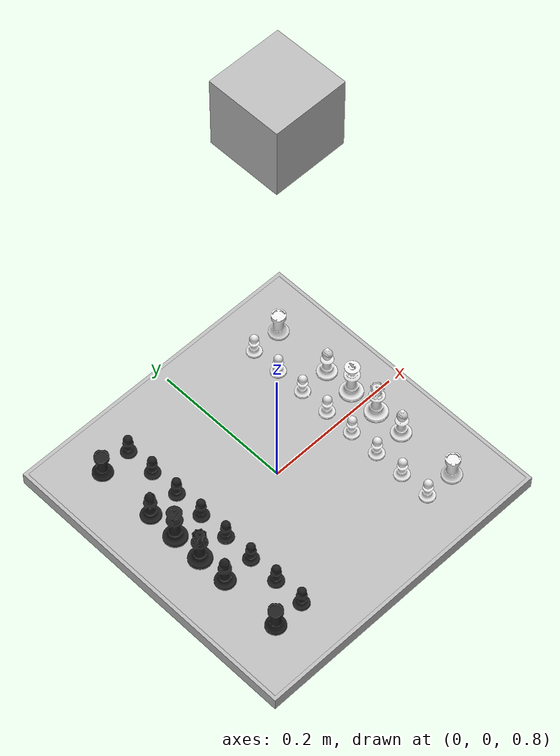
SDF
<sdf version="1.6">
 <world name="ur3_chess_game">
  <gravity>0 0 -9.81</gravity>
  <physics name="default_physics" default="0" type="ode">
   <max_step_size>0.001</max_step_size>
   <real_time_factor>1</real_time_factor>
   <real_time_update_rate>1000</real_time_update_rate>
  </physics>
  <plugin name="ros_link_attacher_plugin" filename="libgazebo_ros_link_attacher.so"/>
  <scene><ambient>0.4 0.4 0.4 1</ambient><background>0.40 0.43 0.67 1</background><shadows>1</shadows></scene>
  <include><uri>model://sun</uri></include>
  <model name="camera">
   <static>1</static>
   <pose>0 0 1.50 3.14 1.57 0</pose>
   <link name="link">
    <visual name="visual"><geometry><box><size>0.1 0.1 0.1</size></box></geometry></visual>
    <sensor name="camera" type="camera">
     <camera>
      <save enabled="1"><path>/tmp/camera_out</path></save>
      <horizontal_fov>1.047</horizontal_fov>
      <image><width>1280</width><height>720</height></image>
      <clip><near>0.1</near><far>100</far></clip>
     </camera>
     <always_on>1</always_on>
     <update_rate>20</update_rate>
     <plugin name="camera_controller" filename="libgazebo_ros_camera.so">
      <alwaysOn>1</alwaysOn>
      <updateRate>0.0</updateRate>
      <cameraName>camera</cameraName>
      <imageTopicName>image_raw</imageTopicName>
      <cameraInfoTopicName>camera_info</cameraInfoTopicName>
      <frameName>camera_link_optical</frameName>
      <hackBaseline>0.0</hackBaseline>
      <distortionK1>0.0</distortionK1>
      <distortionK2>0.0</distortionK2>
      <distortionK3>0.0</distortionK3>
      <distortionT1>0.0</distortionT1>
      <distortionT2>0.0</distortionT2>
      <CxPrime>0</CxPrime>
      <Cx>0.0</Cx>
      <Cy>0.0</Cy>
      <focalLength>0.0</focalLength>
     </plugin>
    </sensor>
   </link>
  </model>
  <model name="chess_board">
   <pose>0 0 0.785 0 0 0</pose>
   <link name="link">
    <inertial>
     <mass>0.5</mass>
     <inertia>
      <ixx>0.166667</ixx>
      <ixy>0</ixy>
      <ixz>0</ixz>
      <iyy>0.166667</iyy>
      <iyz>0</iyz>
      <izz>0.166667</izz>
     </inertia>
    </inertial>
    <visual name="visual">
     <geometry><box><size>0.44 0.44 0.02</size></box></geometry>
     <material>
      <script>
       <name>ChessBoardMaterial</name>
       <uri>model://chess_board/materials/scripts</uri>
       <uri>model://chess_board/materials/textures</uri>
      </script>
     </material>
    </visual>
    <collision name="collision">
     <geometry><box><size>0.44 0.44 0.02</size></box></geometry>
     <surface>
      <friction>
       <ode><mu>1</mu><mu2>1</mu2><fdir1>0 0 0</fdir1><slip1>0</slip1><slip2>0</slip2></ode>
       <torsional>
        <coefficient>1</coefficient>
        <patch_radius>0</patch_radius>
        <surface_radius>0</surface_radius>
        <use_patch_radius>1</use_patch_radius>
        <ode><slip>0</slip></ode>
       </torsional>
      </friction>
      <bounce><restitution_coefficient>0</restitution_coefficient><threshold>1e+06</threshold></bounce>
      <contact>
       <collide_without_contact>0</collide_without_contact>
       <collide_without_contact_bitmask>1</collide_without_contact_bitmask>
       <collide_bitmask>1</collide_bitmask>
       <ode>
        <soft_cfm>0</soft_cfm>
        <soft_erp>0.2</soft_erp>
        <kp>1e+13</kp>
        <kd>1</kd>
        <max_vel>0.01</max_vel>
        <min_depth>0</min_depth>
       </ode>
       <bullet>
        <split_impulse>1</split_impulse>
        <split_impulse_penetration_threshold>-0.01</split_impulse_penetration_threshold>
        <soft_cfm>0</soft_cfm>
        <soft_erp>0.2</soft_erp>
        <kp>1e+13</kp>
        <kd>1</kd>
       </bullet>
      </contact>
     </surface>
    </collision>
   </link>
   <static>0</static>
  </model>
  <model name="chess_board_border">
   <pose>0 0 0.775 0 0 0</pose>
   <link name="chess_board_border">
    <inertial>
     <mass>0.01</mass>
     <inertia>
      <ixx>0.166667</ixx>
      <ixy>0</ixy>
      <ixz>0</ixz>
      <iyy>0.166667</iyy>
      <iyz>0</iyz>
      <izz>0.166667</izz>
     </inertia>
    </inertial>
    <visual name="visual">
     <geometry><mesh><uri>model://chess_board_border/chess_board_border.stl</uri></mesh></geometry>
     <material>
      <script>
       <name>ChessBoardBorderMaterial</name>
       <uri>model://chess_board_border/materials/scripts</uri>
       <uri>model://chess_board_border/materials/textures</uri>
      </script>
     </material>
    </visual>
    <collision name="collision">
     <geometry><mesh><uri>model://chess_board_border/chess_board_border.stl</uri></mesh></geometry>
     <surface>
      <friction>
       <ode><mu>1</mu><mu2>1</mu2><fdir1>0 0 0</fdir1><slip1>0</slip1><slip2>0</slip2></ode>
       <torsional>
        <coefficient>1</coefficient>
        <patch_radius>0</patch_radius>
        <surface_radius>0</surface_radius>
        <use_patch_radius>1</use_patch_radius>
        <ode><slip>0</slip></ode>
       </torsional>
      </friction>
      <bounce><restitution_coefficient>0</restitution_coefficient><threshold>1e+06</threshold></bounce>
      <contact>
       <collide_without_contact>0</collide_without_contact>
       <collide_without_contact_bitmask>1</collide_without_contact_bitmask>
       <collide_bitmask>1</collide_bitmask>
       <ode>
        <soft_cfm>0</soft_cfm>
        <soft_erp>0.2</soft_erp>
        <kp>1e+13</kp>
        <kd>1</kd>
        <max_vel>0.01</max_vel>
        <min_depth>0</min_depth>
       </ode>
       <bullet>
        <split_impulse>1</split_impulse>
        <split_impulse_penetration_threshold>-0.01</split_impulse_penetration_threshold>
        <soft_cfm>0</soft_cfm>
        <soft_erp>0.2</soft_erp>
        <kp>1e+13</kp>
        <kd>1</kd>
       </bullet>
      </contact>
     </surface>
    </collision>
   </link>
   <static>0</static>
  </model>
  <model name="pawn_white_1">
   <pose>0.11 -0.154 0.8 0 0 0</pose>
   <link name="link">
    <inertial>
     <mass>0.1</mass>
     <inertia>
      <ixx>0.166667</ixx>
      <ixy>0</ixy>
      <ixz>0</ixz>
      <iyy>0.166667</iyy>
      <iyz>0</iyz>
      <izz>0.166667</izz>
     </inertia>
    </inertial>
    <visual name="visual">
     <geometry><mesh><uri>model://pawn_white/pawn.stl</uri><scale>0.001 0.001 0.001</scale></mesh></geometry>
     <material>
      <lighting>1</lighting>
      <script><uri>file://media/materials/scripts/gazebo.material</uri><name>Gazebo/White</name></script>
      <shader type="pixel"><normal_map>__default__</normal_map></shader>
      <ambient>1 1 1 1</ambient>
      <diffuse>1 1 1 1</diffuse>
      <specular>0.1 0.1 0.1 1</specular>
      <emissive>0 0 0 1</emissive>
     </material>
    </visual>
    <collision name="collision">
     <geometry><mesh><uri>model://pawn_white/pawn.stl</uri><scale>0.001 0.001 0.001</scale></mesh></geometry>
     <surface>
      <friction>
       <ode><mu>1</mu><mu2>1</mu2><fdir1>0 0 0</fdir1><slip1>0</slip1><slip2>0</slip2></ode>
       <torsional>
        <coefficient>1</coefficient>
        <patch_radius>0</patch_radius>
        <surface_radius>0</surface_radius>
        <use_patch_radius>1</use_patch_radius>
        <ode><slip>0</slip></ode>
       </torsional>
      </friction>
      <bounce><restitution_coefficient>0</restitution_coefficient><threshold>1e+06</threshold></bounce>
      <contact>
       <collide_without_contact>0</collide_without_contact>
       <collide_without_contact_bitmask>1</collide_without_contact_bitmask>
       <collide_bitmask>1</collide_bitmask>
       <ode>
        <soft_cfm>0</soft_cfm>
        <soft_erp>0.2</soft_erp>
        <kp>1e+13</kp>
        <kd>1</kd>
        <max_vel>0.01</max_vel>
        <min_depth>0</min_depth>
       </ode>
       <bullet>
        <split_impulse>1</split_impulse>
        <split_impulse_penetration_threshold>-0.01</split_impulse_penetration_threshold>
        <soft_cfm>0</soft_cfm>
        <soft_erp>0.2</soft_erp>
        <kp>1e+13</kp>
        <kd>1</kd>
       </bullet>
      </contact>
     </surface>
    </collision>
   </link>
   <static>0</static>
  </model>
  <model name="pawn_white_2">
   <pose>0.11 -0.11 0.8 0 0 0</pose>
   <link name="link">
    <inertial>
     <mass>0.1</mass>
     <inertia>
      <ixx>0.166667</ixx>
      <ixy>0</ixy>
      <ixz>0</ixz>
      <iyy>0.166667</iyy>
      <iyz>0</iyz>
      <izz>0.166667</izz>
     </inertia>
    </inertial>
    <visual name="visual">
     <geometry><mesh><uri>model://pawn_white/pawn.stl</uri><scale>0.001 0.001 0.001</scale></mesh></geometry>
     <material>
      <lighting>1</lighting>
      <script><uri>file://media/materials/scripts/gazebo.material</uri><name>Gazebo/White</name></script>
      <shader type="pixel"><normal_map>__default__</normal_map></shader>
      <ambient>1 1 1 1</ambient>
      <diffuse>1 1 1 1</diffuse>
      <specular>0.1 0.1 0.1 1</specular>
      <emissive>0 0 0 1</emissive>
     </material>
    </visual>
    <collision name="collision">
     <geometry><mesh><uri>model://pawn_white/pawn.stl</uri><scale>0.001 0.001 0.001</scale></mesh></geometry>
     <surface>
      <friction>
       <ode><mu>1</mu><mu2>1</mu2><fdir1>0 0 0</fdir1><slip1>0</slip1><slip2>0</slip2></ode>
       <torsional>
        <coefficient>1</coefficient>
        <patch_radius>0</patch_radius>
        <surface_radius>0</surface_radius>
        <use_patch_radius>1</use_patch_radius>
        <ode><slip>0</slip></ode>
       </torsional>
      </friction>
      <bounce><restitution_coefficient>0</restitution_coefficient><threshold>1e+06</threshold></bounce>
      <contact>
       <collide_without_contact>0</collide_without_contact>
       <collide_without_contact_bitmask>1</collide_without_contact_bitmask>
       <collide_bitmask>1</collide_bitmask>
       <ode>
        <soft_cfm>0</soft_cfm>
        <soft_erp>0.2</soft_erp>
        <kp>1e+13</kp>
        <kd>1</kd>
        <max_vel>0.01</max_vel>
        <min_depth>0</min_depth>
       </ode>
       <bullet>
        <split_impulse>1</split_impulse>
        <split_impulse_penetration_threshold>-0.01</split_impulse_penetration_threshold>
        <soft_cfm>0</soft_cfm>
        <soft_erp>0.2</soft_erp>
        <kp>1e+13</kp>
        <kd>1</kd>
       </bullet>
      </contact>
     </surface>
    </collision>
   </link>
   <static>0</static>
  </model>
  <model name="pawn_white_3">
   <pose>0.11 -0.066 0.8 0 0 0</pose>
   <link name="link">
    <inertial>
     <mass>0.1</mass>
     <inertia>
      <ixx>0.166667</ixx>
      <ixy>0</ixy>
      <ixz>0</ixz>
      <iyy>0.166667</iyy>
      <iyz>0</iyz>
      <izz>0.166667</izz>
     </inertia>
    </inertial>
    <visual name="visual">
     <geometry><mesh><uri>model://pawn_white/pawn.stl</uri><scale>0.001 0.001 0.001</scale></mesh></geometry>
     <material>
      <lighting>1</lighting>
      <script><uri>file://media/materials/scripts/gazebo.material</uri><name>Gazebo/White</name></script>
      <shader type="pixel"><normal_map>__default__</normal_map></shader>
      <ambient>1 1 1 1</ambient>
      <diffuse>1 1 1 1</diffuse>
      <specular>0.1 0.1 0.1 1</specular>
      <emissive>0 0 0 1</emissive>
     </material>
    </visual>
    <collision name="collision">
     <geometry><mesh><uri>model://pawn_white/pawn.stl</uri><scale>0.001 0.001 0.001</scale></mesh></geometry>
     <surface>
      <friction>
       <ode><mu>1</mu><mu2>1</mu2><fdir1>0 0 0</fdir1><slip1>0</slip1><slip2>0</slip2></ode>
       <torsional>
        <coefficient>1</coefficient>
        <patch_radius>0</patch_radius>
        <surface_radius>0</surface_radius>
        <use_patch_radius>1</use_patch_radius>
        <ode><slip>0</slip></ode>
       </torsional>
      </friction>
      <bounce><restitution_coefficient>0</restitution_coefficient><threshold>1e+06</threshold></bounce>
      <contact>
       <collide_without_contact>0</collide_without_contact>
       <collide_without_contact_bitmask>1</collide_without_contact_bitmask>
       <collide_bitmask>1</collide_bitmask>
       <ode>
        <soft_cfm>0</soft_cfm>
        <soft_erp>0.2</soft_erp>
        <kp>1e+13</kp>
        <kd>1</kd>
        <max_vel>0.01</max_vel>
        <min_depth>0</min_depth>
       </ode>
       <bullet>
        <split_impulse>1</split_impulse>
        <split_impulse_penetration_threshold>-0.01</split_impulse_penetration_threshold>
        <soft_cfm>0</soft_cfm>
        <soft_erp>0.2</soft_erp>
        <kp>1e+13</kp>
        <kd>1</kd>
       </bullet>
      </contact>
     </surface>
    </collision>
   </link>
   <static>0</static>
  </model>
  <model name="pawn_white_4">
   <pose>0.11 -0.022 0.8 0 0 0</pose>
   <link name="link">
    <inertial>
     <mass>0.1</mass>
     <inertia>
      <ixx>0.166667</ixx>
      <ixy>0</ixy>
      <ixz>0</ixz>
      <iyy>0.166667</iyy>
      <iyz>0</iyz>
      <izz>0.166667</izz>
     </inertia>
    </inertial>
    <visual name="visual">
     <geometry><mesh><uri>model://pawn_white/pawn.stl</uri><scale>0.001 0.001 0.001</scale></mesh></geometry>
     <material>
      <lighting>1</lighting>
      <script><uri>file://media/materials/scripts/gazebo.material</uri><name>Gazebo/White</name></script>
      <shader type="pixel"><normal_map>__default__</normal_map></shader>
      <ambient>1 1 1 1</ambient>
      <diffuse>1 1 1 1</diffuse>
      <specular>0.1 0.1 0.1 1</specular>
      <emissive>0 0 0 1</emissive>
     </material>
    </visual>
    <collision name="collision">
     <geometry><mesh><uri>model://pawn_white/pawn.stl</uri><scale>0.001 0.001 0.001</scale></mesh></geometry>
     <surface>
      <friction>
       <ode><mu>1</mu><mu2>1</mu2><fdir1>0 0 0</fdir1><slip1>0</slip1><slip2>0</slip2></ode>
       <torsional>
        <coefficient>1</coefficient>
        <patch_radius>0</patch_radius>
        <surface_radius>0</surface_radius>
        <use_patch_radius>1</use_patch_radius>
        <ode><slip>0</slip></ode>
       </torsional>
      </friction>
      <bounce><restitution_coefficient>0</restitution_coefficient><threshold>1e+06</threshold></bounce>
      <contact>
       <collide_without_contact>0</collide_without_contact>
       <collide_without_contact_bitmask>1</collide_without_contact_bitmask>
       <collide_bitmask>1</collide_bitmask>
       <ode>
        <soft_cfm>0</soft_cfm>
        <soft_erp>0.2</soft_erp>
        <kp>1e+13</kp>
        <kd>1</kd>
        <max_vel>0.01</max_vel>
        <min_depth>0</min_depth>
       </ode>
       <bullet>
        <split_impulse>1</split_impulse>
        <split_impulse_penetration_threshold>-0.01</split_impulse_penetration_threshold>
        <soft_cfm>0</soft_cfm>
        <soft_erp>0.2</soft_erp>
        <kp>1e+13</kp>
        <kd>1</kd>
       </bullet>
      </contact>
     </surface>
    </collision>
   </link>
   <static>0</static>
  </model>
  <model name="pawn_white_5">
   <pose>0.11 0.022 0.8 0 0 0</pose>
   <link name="link">
    <inertial>
     <mass>0.1</mass>
     <inertia>
      <ixx>0.166667</ixx>
      <ixy>0</ixy>
      <ixz>0</ixz>
      <iyy>0.166667</iyy>
      <iyz>0</iyz>
      <izz>0.166667</izz>
     </inertia>
    </inertial>
    <visual name="visual">
     <geometry><mesh><uri>model://pawn_white/pawn.stl</uri><scale>0.001 0.001 0.001</scale></mesh></geometry>
     <material>
      <lighting>1</lighting>
      <script><uri>file://media/materials/scripts/gazebo.material</uri><name>Gazebo/White</name></script>
      <shader type="pixel"><normal_map>__default__</normal_map></shader>
      <ambient>1 1 1 1</ambient>
      <diffuse>1 1 1 1</diffuse>
      <specular>0.1 0.1 0.1 1</specular>
      <emissive>0 0 0 1</emissive>
     </material>
    </visual>
    <collision name="collision">
     <geometry><mesh><uri>model://pawn_white/pawn.stl</uri><scale>0.001 0.001 0.001</scale></mesh></geometry>
     <surface>
      <friction>
       <ode><mu>1</mu><mu2>1</mu2><fdir1>0 0 0</fdir1><slip1>0</slip1><slip2>0</slip2></ode>
       <torsional>
        <coefficient>1</coefficient>
        <patch_radius>0</patch_radius>
        <surface_radius>0</surface_radius>
        <use_patch_radius>1</use_patch_radius>
        <ode><slip>0</slip></ode>
       </torsional>
      </friction>
      <bounce><restitution_coefficient>0</restitution_coefficient><threshold>1e+06</threshold></bounce>
      <contact>
       <collide_without_contact>0</collide_without_contact>
       <collide_without_contact_bitmask>1</collide_without_contact_bitmask>
       <collide_bitmask>1</collide_bitmask>
       <ode>
        <soft_cfm>0</soft_cfm>
        <soft_erp>0.2</soft_erp>
        <kp>1e+13</kp>
        <kd>1</kd>
        <max_vel>0.01</max_vel>
        <min_depth>0</min_depth>
       </ode>
       <bullet>
        <split_impulse>1</split_impulse>
        <split_impulse_penetration_threshold>-0.01</split_impulse_penetration_threshold>
        <soft_cfm>0</soft_cfm>
        <soft_erp>0.2</soft_erp>
        <kp>1e+13</kp>
        <kd>1</kd>
       </bullet>
      </contact>
     </surface>
    </collision>
   </link>
   <static>0</static>
  </model>
  <model name="pawn_white_6">
   <pose>0.11 0.066 0.8 0 0 0</pose>
   <link name="link">
    <inertial>
     <mass>0.1</mass>
     <inertia>
      <ixx>0.166667</ixx>
      <ixy>0</ixy>
      <ixz>0</ixz>
      <iyy>0.166667</iyy>
      <iyz>0</iyz>
      <izz>0.166667</izz>
     </inertia>
    </inertial>
    <visual name="visual">
     <geometry><mesh><uri>model://pawn_white/pawn.stl</uri><scale>0.001 0.001 0.001</scale></mesh></geometry>
     <material>
      <lighting>1</lighting>
      <script><uri>file://media/materials/scripts/gazebo.material</uri><name>Gazebo/White</name></script>
      <shader type="pixel"><normal_map>__default__</normal_map></shader>
      <ambient>1 1 1 1</ambient>
      <diffuse>1 1 1 1</diffuse>
      <specular>0.1 0.1 0.1 1</specular>
      <emissive>0 0 0 1</emissive>
     </material>
    </visual>
    <collision name="collision">
     <geometry><mesh><uri>model://pawn_white/pawn.stl</uri><scale>0.001 0.001 0.001</scale></mesh></geometry>
     <surface>
      <friction>
       <ode><mu>1</mu><mu2>1</mu2><fdir1>0 0 0</fdir1><slip1>0</slip1><slip2>0</slip2></ode>
       <torsional>
        <coefficient>1</coefficient>
        <patch_radius>0</patch_radius>
        <surface_radius>0</surface_radius>
        <use_patch_radius>1</use_patch_radius>
        <ode><slip>0</slip></ode>
       </torsional>
      </friction>
      <bounce><restitution_coefficient>0</restitution_coefficient><threshold>1e+06</threshold></bounce>
      <contact>
       <collide_without_contact>0</collide_without_contact>
       <collide_without_contact_bitmask>1</collide_without_contact_bitmask>
       <collide_bitmask>1</collide_bitmask>
       <ode>
        <soft_cfm>0</soft_cfm>
        <soft_erp>0.2</soft_erp>
        <kp>1e+13</kp>
        <kd>1</kd>
        <max_vel>0.01</max_vel>
        <min_depth>0</min_depth>
       </ode>
       <bullet>
        <split_impulse>1</split_impulse>
        <split_impulse_penetration_threshold>-0.01</split_impulse_penetration_threshold>
        <soft_cfm>0</soft_cfm>
        <soft_erp>0.2</soft_erp>
        <kp>1e+13</kp>
        <kd>1</kd>
       </bullet>
      </contact>
     </surface>
    </collision>
   </link>
   <static>0</static>
  </model>
  <model name="pawn_white_7">
   <pose>0.11 0.11 0.8 0 0 0</pose>
   <link name="link">
    <inertial>
     <mass>0.1</mass>
     <inertia>
      <ixx>0.166667</ixx>
      <ixy>0</ixy>
      <ixz>0</ixz>
      <iyy>0.166667</iyy>
      <iyz>0</iyz>
      <izz>0.166667</izz>
     </inertia>
    </inertial>
    <visual name="visual">
     <geometry><mesh><uri>model://pawn_white/pawn.stl</uri><scale>0.001 0.001 0.001</scale></mesh></geometry>
     <material>
      <lighting>1</lighting>
      <script><uri>file://media/materials/scripts/gazebo.material</uri><name>Gazebo/White</name></script>
      <shader type="pixel"><normal_map>__default__</normal_map></shader>
      <ambient>1 1 1 1</ambient>
      <diffuse>1 1 1 1</diffuse>
      <specular>0.1 0.1 0.1 1</specular>
      <emissive>0 0 0 1</emissive>
     </material>
    </visual>
    <collision name="collision">
     <geometry><mesh><uri>model://pawn_white/pawn.stl</uri><scale>0.001 0.001 0.001</scale></mesh></geometry>
     <surface>
      <friction>
       <ode><mu>1</mu><mu2>1</mu2><fdir1>0 0 0</fdir1><slip1>0</slip1><slip2>0</slip2></ode>
       <torsional>
        <coefficient>1</coefficient>
        <patch_radius>0</patch_radius>
        <surface_radius>0</surface_radius>
        <use_patch_radius>1</use_patch_radius>
        <ode><slip>0</slip></ode>
       </torsional>
      </friction>
      <bounce><restitution_coefficient>0</restitution_coefficient><threshold>1e+06</threshold></bounce>
      <contact>
       <collide_without_contact>0</collide_without_contact>
       <collide_without_contact_bitmask>1</collide_without_contact_bitmask>
       <collide_bitmask>1</collide_bitmask>
       <ode>
        <soft_cfm>0</soft_cfm>
        <soft_erp>0.2</soft_erp>
        <kp>1e+13</kp>
        <kd>1</kd>
        <max_vel>0.01</max_vel>
        <min_depth>0</min_depth>
       </ode>
       <bullet>
        <split_impulse>1</split_impulse>
        <split_impulse_penetration_threshold>-0.01</split_impulse_penetration_threshold>
        <soft_cfm>0</soft_cfm>
        <soft_erp>0.2</soft_erp>
        <kp>1e+13</kp>
        <kd>1</kd>
       </bullet>
      </contact>
     </surface>
    </collision>
   </link>
   <static>0</static>
  </model>
  <model name="pawn_white_8">
   <pose>0.11 0.154 0.8 0 0 0</pose>
   <link name="link">
    <inertial>
     <mass>0.1</mass>
     <inertia>
      <ixx>0.166667</ixx>
      <ixy>0</ixy>
      <ixz>0</ixz>
      <iyy>0.166667</iyy>
      <iyz>0</iyz>
      <izz>0.166667</izz>
     </inertia>
    </inertial>
    <visual name="visual">
     <geometry><mesh><uri>model://pawn_white/pawn.stl</uri><scale>0.001 0.001 0.001</scale></mesh></geometry>
     <material>
      <lighting>1</lighting>
      <script><uri>file://media/materials/scripts/gazebo.material</uri><name>Gazebo/White</name></script>
      <shader type="pixel"><normal_map>__default__</normal_map></shader>
      <ambient>1 1 1 1</ambient>
      <diffuse>1 1 1 1</diffuse>
      <specular>0.1 0.1 0.1 1</specular>
      <emissive>0 0 0 1</emissive>
     </material>
    </visual>
    <collision name="collision">
     <geometry><mesh><uri>model://pawn_white/pawn.stl</uri><scale>0.001 0.001 0.001</scale></mesh></geometry>
     <surface>
      <friction>
       <ode><mu>1</mu><mu2>1</mu2><fdir1>0 0 0</fdir1><slip1>0</slip1><slip2>0</slip2></ode>
       <torsional>
        <coefficient>1</coefficient>
        <patch_radius>0</patch_radius>
        <surface_radius>0</surface_radius>
        <use_patch_radius>1</use_patch_radius>
        <ode><slip>0</slip></ode>
       </torsional>
      </friction>
      <bounce><restitution_coefficient>0</restitution_coefficient><threshold>1e+06</threshold></bounce>
      <contact>
       <collide_without_contact>0</collide_without_contact>
       <collide_without_contact_bitmask>1</collide_without_contact_bitmask>
       <collide_bitmask>1</collide_bitmask>
       <ode>
        <soft_cfm>0</soft_cfm>
        <soft_erp>0.2</soft_erp>
        <kp>1e+13</kp>
        <kd>1</kd>
        <max_vel>0.01</max_vel>
        <min_depth>0</min_depth>
       </ode>
       <bullet>
        <split_impulse>1</split_impulse>
        <split_impulse_penetration_threshold>-0.01</split_impulse_penetration_threshold>
        <soft_cfm>0</soft_cfm>
        <soft_erp>0.2</soft_erp>
        <kp>1e+13</kp>
        <kd>1</kd>
       </bullet>
      </contact>
     </surface>
    </collision>
   </link>
   <static>0</static>
  </model>
  <model name="rook_white_1">
   <pose>0.154 -0.154 0.8 0 0 0</pose>
   <link name="link">
    <inertial>
     <mass>0.1</mass>
     <inertia>
      <ixx>0.166667</ixx>
      <ixy>0</ixy>
      <ixz>0</ixz>
      <iyy>0.166667</iyy>
      <iyz>0</iyz>
      <izz>0.166667</izz>
     </inertia>
    </inertial>
    <visual name="visual">
     <geometry><mesh><uri>model://rook_white/rook.stl</uri><scale>0.001 0.001 0.001</scale></mesh></geometry>
     <material>
      <lighting>1</lighting>
      <script><uri>file://media/materials/scripts/gazebo.material</uri><name>Gazebo/White</name></script>
      <shader type="pixel"><normal_map>__default__</normal_map></shader>
      <ambient>1 1 1 1</ambient>
      <diffuse>1 1 1 1</diffuse>
      <specular>0.1 0.1 0.1 1</specular>
      <emissive>0 0 0 1</emissive>
     </material>
    </visual>
    <collision name="collision">
     <geometry><mesh><uri>model://rook_white/rook.stl</uri><scale>0.001 0.001 0.001</scale></mesh></geometry>
     <surface>
      <friction>
       <ode><mu>1</mu><mu2>1</mu2><fdir1>0 0 0</fdir1><slip1>0</slip1><slip2>0</slip2></ode>
       <torsional>
        <coefficient>1</coefficient>
        <patch_radius>0</patch_radius>
        <surface_radius>0</surface_radius>
        <use_patch_radius>1</use_patch_radius>
        <ode><slip>0</slip></ode>
       </torsional>
      </friction>
      <bounce><restitution_coefficient>0</restitution_coefficient><threshold>1e+06</threshold></bounce>
      <contact>
       <collide_without_contact>0</collide_without_contact>
       <collide_without_contact_bitmask>1</collide_without_contact_bitmask>
       <collide_bitmask>1</collide_bitmask>
       <ode>
        <soft_cfm>0</soft_cfm>
        <soft_erp>0.2</soft_erp>
        <kp>1e+13</kp>
        <kd>1</kd>
        <max_vel>0.01</max_vel>
        <min_depth>0</min_depth>
       </ode>
       <bullet>
        <split_impulse>1</split_impulse>
        <split_impulse_penetration_threshold>-0.01</split_impulse_penetration_threshold>
        <soft_cfm>0</soft_cfm>
        <soft_erp>0.2</soft_erp>
        <kp>1e+13</kp>
        <kd>1</kd>
       </bullet>
      </contact>
     </surface>
    </collision>
   </link>
   <static>0</static>
  </model>
  <model name="rook_white_2">
   <pose>0.154 0.154 0.8 0 0 0</pose>
   <link name="link">
    <inertial>
     <mass>0.1</mass>
     <inertia>
      <ixx>0.166667</ixx>
      <ixy>0</ixy>
      <ixz>0</ixz>
      <iyy>0.166667</iyy>
      <iyz>0</iyz>
      <izz>0.166667</izz>
     </inertia>
    </inertial>
    <visual name="visual">
     <geometry><mesh><uri>model://rook_white/rook.stl</uri><scale>0.001 0.001 0.001</scale></mesh></geometry>
     <material>
      <lighting>1</lighting>
      <script><uri>file://media/materials/scripts/gazebo.material</uri><name>Gazebo/White</name></script>
      <shader type="pixel"><normal_map>__default__</normal_map></shader>
      <ambient>1 1 1 1</ambient>
      <diffuse>1 1 1 1</diffuse>
      <specular>0.1 0.1 0.1 1</specular>
      <emissive>0 0 0 1</emissive>
     </material>
    </visual>
    <collision name="collision">
     <geometry><mesh><uri>model://rook_white/rook.stl</uri><scale>0.001 0.001 0.001</scale></mesh></geometry>
     <surface>
      <friction>
       <ode><mu>1</mu><mu2>1</mu2><fdir1>0 0 0</fdir1><slip1>0</slip1><slip2>0</slip2></ode>
       <torsional>
        <coefficient>1</coefficient>
        <patch_radius>0</patch_radius>
        <surface_radius>0</surface_radius>
        <use_patch_radius>1</use_patch_radius>
        <ode><slip>0</slip></ode>
       </torsional>
      </friction>
      <bounce><restitution_coefficient>0</restitution_coefficient><threshold>1e+06</threshold></bounce>
      <contact>
       <collide_without_contact>0</collide_without_contact>
       <collide_without_contact_bitmask>1</collide_without_contact_bitmask>
       <collide_bitmask>1</collide_bitmask>
       <ode>
        <soft_cfm>0</soft_cfm>
        <soft_erp>0.2</soft_erp>
        <kp>1e+13</kp>
        <kd>1</kd>
        <max_vel>0.01</max_vel>
        <min_depth>0</min_depth>
       </ode>
       <bullet>
        <split_impulse>1</split_impulse>
        <split_impulse_penetration_threshold>-0.01</split_impulse_penetration_threshold>
        <soft_cfm>0</soft_cfm>
        <soft_erp>0.2</soft_erp>
        <kp>1e+13</kp>
        <kd>1</kd>
       </bullet>
      </contact>
     </surface>
    </collision>
   </link>
   <static>0</static>
  </model>
  <model name="bishop_white_1">
   <pose>0.154 -0.066 0.8 0 0 0</pose>
   <link name="link">
    <inertial>
     <mass>0.1</mass>
     <inertia>
      <ixx>0.166667</ixx>
      <ixy>0</ixy>
      <ixz>0</ixz>
      <iyy>0.166667</iyy>
      <iyz>0</iyz>
      <izz>0.166667</izz>
     </inertia>
    </inertial>
    <visual name="visual">
     <geometry><mesh><uri>model://bishop_white/bishop.stl</uri><scale>0.001 0.001 0.001</scale></mesh></geometry>
     <material>
      <lighting>1</lighting>
      <script><uri>file://media/materials/scripts/gazebo.material</uri><name>Gazebo/White</name></script>
      <shader type="pixel"><normal_map>__default__</normal_map></shader>
      <ambient>1 1 1 1</ambient>
      <diffuse>1 1 1 1</diffuse>
      <specular>0.1 0.1 0.1 1</specular>
      <emissive>0 0 0 1</emissive>
     </material>
    </visual>
    <collision name="collision">
     <geometry><mesh><uri>model://bishop_white/bishop.stl</uri><scale>0.001 0.001 0.001</scale></mesh></geometry>
     <surface>
      <friction>
       <ode><mu>1</mu><mu2>1</mu2><fdir1>0 0 0</fdir1><slip1>0</slip1><slip2>0</slip2></ode>
       <torsional>
        <coefficient>1</coefficient>
        <patch_radius>0</patch_radius>
        <surface_radius>0</surface_radius>
        <use_patch_radius>1</use_patch_radius>
        <ode><slip>0</slip></ode>
       </torsional>
      </friction>
      <bounce><restitution_coefficient>0</restitution_coefficient><threshold>1e+06</threshold></bounce>
      <contact>
       <collide_without_contact>0</collide_without_contact>
       <collide_without_contact_bitmask>1</collide_without_contact_bitmask>
       <collide_bitmask>1</collide_bitmask>
       <ode>
        <soft_cfm>0</soft_cfm>
        <soft_erp>0.2</soft_erp>
        <kp>1e+13</kp>
        <kd>1</kd>
        <max_vel>0.01</max_vel>
        <min_depth>0</min_depth>
       </ode>
       <bullet>
        <split_impulse>1</split_impulse>
        <split_impulse_penetration_threshold>-0.01</split_impulse_penetration_threshold>
        <soft_cfm>0</soft_cfm>
        <soft_erp>0.2</soft_erp>
        <kp>1e+13</kp>
        <kd>1</kd>
       </bullet>
      </contact>
     </surface>
    </collision>
   </link>
   <static>0</static>
  </model>
  <model name="bishop_white_2">
   <pose>0.154 0.066 0.8 0 0 0</pose>
   <link name="link">
    <inertial>
     <mass>0.1</mass>
     <inertia>
      <ixx>0.166667</ixx>
      <ixy>0</ixy>
      <ixz>0</ixz>
      <iyy>0.166667</iyy>
      <iyz>0</iyz>
      <izz>0.166667</izz>
     </inertia>
    </inertial>
    <visual name="visual">
     <geometry><mesh><uri>model://bishop_white/bishop.stl</uri><scale>0.001 0.001 0.001</scale></mesh></geometry>
     <material>
      <lighting>1</lighting>
      <script><uri>file://media/materials/scripts/gazebo.material</uri><name>Gazebo/White</name></script>
      <shader type="pixel"><normal_map>__default__</normal_map></shader>
      <ambient>1 1 1 1</ambient>
      <diffuse>1 1 1 1</diffuse>
      <specular>0.1 0.1 0.1 1</specular>
      <emissive>0 0 0 1</emissive>
     </material>
    </visual>
    <collision name="collision">
     <geometry><mesh><uri>model://bishop_white/bishop.stl</uri><scale>0.001 0.001 0.001</scale></mesh></geometry>
     <surface>
      <friction>
       <ode><mu>1</mu><mu2>1</mu2><fdir1>0 0 0</fdir1><slip1>0</slip1><slip2>0</slip2></ode>
       <torsional>
        <coefficient>1</coefficient>
        <patch_radius>0</patch_radius>
        <surface_radius>0</surface_radius>
        <use_patch_radius>1</use_patch_radius>
        <ode><slip>0</slip></ode>
       </torsional>
      </friction>
      <bounce><restitution_coefficient>0</restitution_coefficient><threshold>1e+06</threshold></bounce>
      <contact>
       <collide_without_contact>0</collide_without_contact>
       <collide_without_contact_bitmask>1</collide_without_contact_bitmask>
       <collide_bitmask>1</collide_bitmask>
       <ode>
        <soft_cfm>0</soft_cfm>
        <soft_erp>0.2</soft_erp>
        <kp>1e+13</kp>
        <kd>1</kd>
        <max_vel>0.01</max_vel>
        <min_depth>0</min_depth>
       </ode>
       <bullet>
        <split_impulse>1</split_impulse>
        <split_impulse_penetration_threshold>-0.01</split_impulse_penetration_threshold>
        <soft_cfm>0</soft_cfm>
        <soft_erp>0.2</soft_erp>
        <kp>1e+13</kp>
        <kd>1</kd>
       </bullet>
      </contact>
     </surface>
    </collision>
   </link>
   <static>0</static>
  </model>
  <model name="queen_white">
   <pose>0.154 -0.022 0.8 0 0 0</pose>
   <link name="link">
    <inertial>
     <mass>0.1</mass>
     <inertia>
      <ixx>0.166667</ixx>
      <ixy>0</ixy>
      <ixz>0</ixz>
      <iyy>0.166667</iyy>
      <iyz>0</iyz>
      <izz>0.166667</izz>
     </inertia>
    </inertial>
    <visual name="visual">
     <geometry><mesh><uri>model://queen_white/queen.stl</uri><scale>0.001 0.001 0.001</scale></mesh></geometry>
     <material>
      <lighting>1</lighting>
      <script><uri>file://media/materials/scripts/gazebo.material</uri><name>Gazebo/White</name></script>
      <shader type="pixel"><normal_map>__default__</normal_map></shader>
      <ambient>1 1 1 1</ambient>
      <diffuse>1 1 1 1</diffuse>
      <specular>0.1 0.1 0.1 1</specular>
      <emissive>0 0 0 1</emissive>
     </material>
    </visual>
    <collision name="collision">
     <geometry><mesh><uri>model://queen_white/queen.stl</uri><scale>0.001 0.001 0.001</scale></mesh></geometry>
     <surface>
      <friction>
       <ode><mu>1</mu><mu2>1</mu2><fdir1>0 0 0</fdir1><slip1>0</slip1><slip2>0</slip2></ode>
       <torsional>
        <coefficient>1</coefficient>
        <patch_radius>0</patch_radius>
        <surface_radius>0</surface_radius>
        <use_patch_radius>1</use_patch_radius>
        <ode><slip>0</slip></ode>
       </torsional>
      </friction>
      <bounce><restitution_coefficient>0</restitution_coefficient><threshold>1e+06</threshold></bounce>
      <contact>
       <collide_without_contact>0</collide_without_contact>
       <collide_without_contact_bitmask>1</collide_without_contact_bitmask>
       <collide_bitmask>1</collide_bitmask>
       <ode>
        <soft_cfm>0</soft_cfm>
        <soft_erp>0.2</soft_erp>
        <kp>1e+13</kp>
        <kd>1</kd>
        <max_vel>0.01</max_vel>
        <min_depth>0</min_depth>
       </ode>
       <bullet>
        <split_impulse>1</split_impulse>
        <split_impulse_penetration_threshold>-0.01</split_impulse_penetration_threshold>
        <soft_cfm>0</soft_cfm>
        <soft_erp>0.2</soft_erp>
        <kp>1e+13</kp>
        <kd>1</kd>
       </bullet>
      </contact>
     </surface>
    </collision>
   </link>
   <static>0</static>
  </model>
  <model name="king_white">
   <pose>0.154 0.022 0.8 0 0 1.57</pose>
   <link name="link">
    <inertial>
     <mass>0.1</mass>
     <inertia>
      <ixx>0.166667</ixx>
      <ixy>0</ixy>
      <ixz>0</ixz>
      <iyy>0.166667</iyy>
      <iyz>0</iyz>
      <izz>0.166667</izz>
     </inertia>
    </inertial>
    <visual name="visual">
     <geometry><mesh><uri>model://king_white/king.stl</uri><scale>0.001 0.001 0.001</scale></mesh></geometry>
     <material>
      <lighting>1</lighting>
      <script><uri>file://media/materials/scripts/gazebo.material</uri><name>Gazebo/White</name></script>
      <shader type="pixel"><normal_map>__default__</normal_map></shader>
      <ambient>1 1 1 1</ambient>
      <diffuse>1 1 1 1</diffuse>
      <specular>0.1 0.1 0.1 1</specular>
      <emissive>0 0 0 1</emissive>
     </material>
    </visual>
    <collision name="collision">
     <geometry><mesh><uri>model://king_white/king.stl</uri><scale>0.001 0.001 0.001</scale></mesh></geometry>
     <surface>
      <friction>
       <ode><mu>1</mu><mu2>1</mu2><fdir1>0 0 0</fdir1><slip1>0</slip1><slip2>0</slip2></ode>
       <torsional>
        <coefficient>1</coefficient>
        <patch_radius>0</patch_radius>
        <surface_radius>0</surface_radius>
        <use_patch_radius>1</use_patch_radius>
        <ode><slip>0</slip></ode>
       </torsional>
      </friction>
      <bounce><restitution_coefficient>0</restitution_coefficient><threshold>1e+06</threshold></bounce>
      <contact>
       <collide_without_contact>0</collide_without_contact>
       <collide_without_contact_bitmask>1</collide_without_contact_bitmask>
       <collide_bitmask>1</collide_bitmask>
       <ode>
        <soft_cfm>0</soft_cfm>
        <soft_erp>0.2</soft_erp>
        <kp>1e+13</kp>
        <kd>1</kd>
        <max_vel>0.01</max_vel>
        <min_depth>0</min_depth>
       </ode>
       <bullet>
        <split_impulse>1</split_impulse>
        <split_impulse_penetration_threshold>-0.01</split_impulse_penetration_threshold>
        <soft_cfm>0</soft_cfm>
        <soft_erp>0.2</soft_erp>
        <kp>1e+13</kp>
        <kd>1</kd>
       </bullet>
      </contact>
     </surface>
    </collision>
   </link>
   <static>0</static>
  </model>
  <model name="pawn_black_1">
   <pose>-0.11 0.154 0.8 0 0 0</pose>
   <link name="link">
    <inertial>
     <mass>0.1</mass>
     <inertia>
      <ixx>0.166667</ixx>
      <ixy>0</ixy>
      <ixz>0</ixz>
      <iyy>0.166667</iyy>
      <iyz>0</iyz>
      <izz>0.166667</izz>
     </inertia>
    </inertial>
    <visual name="visual">
     <geometry><mesh><uri>model://pawn_black/pawn.stl</uri><scale>0.001 0.001 0.001</scale></mesh></geometry>
     <material>
      <lighting>1</lighting>
      <script><uri>file://media/materials/scripts/gazebo.material</uri><name>Gazebo/Black</name></script>
      <shader type="pixel"><normal_map>__default__</normal_map></shader>
      <ambient>0.3 0.3 0.3 1</ambient>
      <diffuse>0.3 0.3 0.3 1</diffuse>
      <specular>0.1 0.1 0.1 1</specular>
      <emissive>0 0 0 1</emissive>
     </material>
    </visual>
    <collision name="collision">
     <geometry><mesh><uri>model://pawn_black/pawn.stl</uri><scale>0.001 0.001 0.001</scale></mesh></geometry>
     <surface>
      <friction>
       <ode><mu>1</mu><mu2>1</mu2><fdir1>0 0 0</fdir1><slip1>0</slip1><slip2>0</slip2></ode>
       <torsional>
        <coefficient>1</coefficient>
        <patch_radius>0</patch_radius>
        <surface_radius>0</surface_radius>
        <use_patch_radius>1</use_patch_radius>
        <ode><slip>0</slip></ode>
       </torsional>
      </friction>
      <bounce><restitution_coefficient>0</restitution_coefficient><threshold>1e+06</threshold></bounce>
      <contact>
       <collide_without_contact>0</collide_without_contact>
       <collide_without_contact_bitmask>1</collide_without_contact_bitmask>
       <collide_bitmask>1</collide_bitmask>
       <ode>
        <soft_cfm>0</soft_cfm>
        <soft_erp>0.2</soft_erp>
        <kp>1e+13</kp>
        <kd>1</kd>
        <max_vel>0.01</max_vel>
        <min_depth>0</min_depth>
       </ode>
       <bullet>
        <split_impulse>1</split_impulse>
        <split_impulse_penetration_threshold>-0.01</split_impulse_penetration_threshold>
        <soft_cfm>0</soft_cfm>
        <soft_erp>0.2</soft_erp>
        <kp>1e+13</kp>
        <kd>1</kd>
       </bullet>
      </contact>
     </surface>
    </collision>
   </link>
   <static>0</static>
  </model>
  <model name="pawn_black_2">
   <pose>-0.11 0.11 0.8 0 0 0</pose>
   <link name="link">
    <inertial>
     <mass>0.1</mass>
     <inertia>
      <ixx>0.166667</ixx>
      <ixy>0</ixy>
      <ixz>0</ixz>
      <iyy>0.166667</iyy>
      <iyz>0</iyz>
      <izz>0.166667</izz>
     </inertia>
    </inertial>
    <visual name="visual">
     <geometry><mesh><uri>model://pawn_black/pawn.stl</uri><scale>0.001 0.001 0.001</scale></mesh></geometry>
     <material>
      <lighting>1</lighting>
      <script><uri>file://media/materials/scripts/gazebo.material</uri><name>Gazebo/Black</name></script>
      <shader type="pixel"><normal_map>__default__</normal_map></shader>
      <ambient>0.3 0.3 0.3 1</ambient>
      <diffuse>0.3 0.3 0.3 1</diffuse>
      <specular>0.1 0.1 0.1 1</specular>
      <emissive>0 0 0 1</emissive>
     </material>
    </visual>
    <collision name="collision">
     <geometry><mesh><uri>model://pawn_black/pawn.stl</uri><scale>0.001 0.001 0.001</scale></mesh></geometry>
     <surface>
      <friction>
       <ode><mu>1</mu><mu2>1</mu2><fdir1>0 0 0</fdir1><slip1>0</slip1><slip2>0</slip2></ode>
       <torsional>
        <coefficient>1</coefficient>
        <patch_radius>0</patch_radius>
        <surface_radius>0</surface_radius>
        <use_patch_radius>1</use_patch_radius>
        <ode><slip>0</slip></ode>
       </torsional>
      </friction>
      <bounce><restitution_coefficient>0</restitution_coefficient><threshold>1e+06</threshold></bounce>
      <contact>
       <collide_without_contact>0</collide_without_contact>
       <collide_without_contact_bitmask>1</collide_without_contact_bitmask>
       <collide_bitmask>1</collide_bitmask>
       <ode>
        <soft_cfm>0</soft_cfm>
        <soft_erp>0.2</soft_erp>
        <kp>1e+13</kp>
        <kd>1</kd>
        <max_vel>0.01</max_vel>
        <min_depth>0</min_depth>
       </ode>
       <bullet>
        <split_impulse>1</split_impulse>
        <split_impulse_penetration_threshold>-0.01</split_impulse_penetration_threshold>
        <soft_cfm>0</soft_cfm>
        <soft_erp>0.2</soft_erp>
        <kp>1e+13</kp>
        <kd>1</kd>
       </bullet>
      </contact>
     </surface>
    </collision>
   </link>
   <static>0</static>
  </model>
  <model name="pawn_black_3">
   <pose>-0.11 0.066 0.8 0 0 0</pose>
   <link name="link">
    <inertial>
     <mass>0.1</mass>
     <inertia>
      <ixx>0.166667</ixx>
      <ixy>0</ixy>
      <ixz>0</ixz>
      <iyy>0.166667</iyy>
      <iyz>0</iyz>
      <izz>0.166667</izz>
     </inertia>
    </inertial>
    <visual name="visual">
     <geometry><mesh><uri>model://pawn_black/pawn.stl</uri><scale>0.001 0.001 0.001</scale></mesh></geometry>
     <material>
      <lighting>1</lighting>
      <script><uri>file://media/materials/scripts/gazebo.material</uri><name>Gazebo/Black</name></script>
      <shader type="pixel"><normal_map>__default__</normal_map></shader>
      <ambient>0.3 0.3 0.3 1</ambient>
      <diffuse>0.3 0.3 0.3 1</diffuse>
      <specular>0.1 0.1 0.1 1</specular>
      <emissive>0 0 0 1</emissive>
     </material>
    </visual>
    <collision name="collision">
     <geometry><mesh><uri>model://pawn_black/pawn.stl</uri><scale>0.001 0.001 0.001</scale></mesh></geometry>
     <surface>
      <friction>
       <ode><mu>1</mu><mu2>1</mu2><fdir1>0 0 0</fdir1><slip1>0</slip1><slip2>0</slip2></ode>
       <torsional>
        <coefficient>1</coefficient>
        <patch_radius>0</patch_radius>
        <surface_radius>0</surface_radius>
        <use_patch_radius>1</use_patch_radius>
        <ode><slip>0</slip></ode>
       </torsional>
      </friction>
      <bounce><restitution_coefficient>0</restitution_coefficient><threshold>1e+06</threshold></bounce>
      <contact>
       <collide_without_contact>0</collide_without_contact>
       <collide_without_contact_bitmask>1</collide_without_contact_bitmask>
       <collide_bitmask>1</collide_bitmask>
       <ode>
        <soft_cfm>0</soft_cfm>
        <soft_erp>0.2</soft_erp>
        <kp>1e+13</kp>
        <kd>1</kd>
        <max_vel>0.01</max_vel>
        <min_depth>0</min_depth>
       </ode>
       <bullet>
        <split_impulse>1</split_impulse>
        <split_impulse_penetration_threshold>-0.01</split_impulse_penetration_threshold>
        <soft_cfm>0</soft_cfm>
        <soft_erp>0.2</soft_erp>
        <kp>1e+13</kp>
        <kd>1</kd>
       </bullet>
      </contact>
     </surface>
    </collision>
   </link>
   <static>0</static>
  </model>
  <model name="pawn_black_4">
   <pose>-0.11 0.022 0.8 0 0 0</pose>
   <link name="link">
    <inertial>
     <mass>0.1</mass>
     <inertia>
      <ixx>0.166667</ixx>
      <ixy>0</ixy>
      <ixz>0</ixz>
      <iyy>0.166667</iyy>
      <iyz>0</iyz>
      <izz>0.166667</izz>
     </inertia>
    </inertial>
    <visual name="visual">
     <geometry><mesh><uri>model://pawn_black/pawn.stl</uri><scale>0.001 0.001 0.001</scale></mesh></geometry>
     <material>
      <lighting>1</lighting>
      <script><uri>file://media/materials/scripts/gazebo.material</uri><name>Gazebo/Black</name></script>
      <shader type="pixel"><normal_map>__default__</normal_map></shader>
      <ambient>0.3 0.3 0.3 1</ambient>
      <diffuse>0.3 0.3 0.3 1</diffuse>
      <specular>0.1 0.1 0.1 1</specular>
      <emissive>0 0 0 1</emissive>
     </material>
    </visual>
    <collision name="collision">
     <geometry><mesh><uri>model://pawn_black/pawn.stl</uri><scale>0.001 0.001 0.001</scale></mesh></geometry>
     <surface>
      <friction>
       <ode><mu>1</mu><mu2>1</mu2><fdir1>0 0 0</fdir1><slip1>0</slip1><slip2>0</slip2></ode>
       <torsional>
        <coefficient>1</coefficient>
        <patch_radius>0</patch_radius>
        <surface_radius>0</surface_radius>
        <use_patch_radius>1</use_patch_radius>
        <ode><slip>0</slip></ode>
       </torsional>
      </friction>
      <bounce><restitution_coefficient>0</restitution_coefficient><threshold>1e+06</threshold></bounce>
      <contact>
       <collide_without_contact>0</collide_without_contact>
       <collide_without_contact_bitmask>1</collide_without_contact_bitmask>
       <collide_bitmask>1</collide_bitmask>
       <ode>
        <soft_cfm>0</soft_cfm>
        <soft_erp>0.2</soft_erp>
        <kp>1e+13</kp>
        <kd>1</kd>
        <max_vel>0.01</max_vel>
        <min_depth>0</min_depth>
       </ode>
       <bullet>
        <split_impulse>1</split_impulse>
        <split_impulse_penetration_threshold>-0.01</split_impulse_penetration_threshold>
        <soft_cfm>0</soft_cfm>
        <soft_erp>0.2</soft_erp>
        <kp>1e+13</kp>
        <kd>1</kd>
       </bullet>
      </contact>
     </surface>
    </collision>
   </link>
   <static>0</static>
  </model>
  <model name="pawn_black_5">
   <pose>-0.11 -0.022 0.8 0 0 0</pose>
   <link name="link">
    <inertial>
     <mass>0.1</mass>
     <inertia>
      <ixx>0.166667</ixx>
      <ixy>0</ixy>
      <ixz>0</ixz>
      <iyy>0.166667</iyy>
      <iyz>0</iyz>
      <izz>0.166667</izz>
     </inertia>
    </inertial>
    <visual name="visual">
     <geometry><mesh><uri>model://pawn_black/pawn.stl</uri><scale>0.001 0.001 0.001</scale></mesh></geometry>
     <material>
      <lighting>1</lighting>
      <script><uri>file://media/materials/scripts/gazebo.material</uri><name>Gazebo/Black</name></script>
      <shader type="pixel"><normal_map>__default__</normal_map></shader>
      <ambient>0.3 0.3 0.3 1</ambient>
      <diffuse>0.3 0.3 0.3 1</diffuse>
      <specular>0.1 0.1 0.1 1</specular>
      <emissive>0 0 0 1</emissive>
     </material>
    </visual>
    <collision name="collision">
     <geometry><mesh><uri>model://pawn_black/pawn.stl</uri><scale>0.001 0.001 0.001</scale></mesh></geometry>
     <surface>
      <friction>
       <ode><mu>1</mu><mu2>1</mu2><fdir1>0 0 0</fdir1><slip1>0</slip1><slip2>0</slip2></ode>
       <torsional>
        <coefficient>1</coefficient>
        <patch_radius>0</patch_radius>
        <surface_radius>0</surface_radius>
        <use_patch_radius>1</use_patch_radius>
        <ode><slip>0</slip></ode>
       </torsional>
      </friction>
      <bounce><restitution_coefficient>0</restitution_coefficient><threshold>1e+06</threshold></bounce>
      <contact>
       <collide_without_contact>0</collide_without_contact>
       <collide_without_contact_bitmask>1</collide_without_contact_bitmask>
       <collide_bitmask>1</collide_bitmask>
       <ode>
        <soft_cfm>0</soft_cfm>
        <soft_erp>0.2</soft_erp>
        <kp>1e+13</kp>
        <kd>1</kd>
        <max_vel>0.01</max_vel>
        <min_depth>0</min_depth>
       </ode>
       <bullet>
        <split_impulse>1</split_impulse>
        <split_impulse_penetration_threshold>-0.01</split_impulse_penetration_threshold>
        <soft_cfm>0</soft_cfm>
        <soft_erp>0.2</soft_erp>
        <kp>1e+13</kp>
        <kd>1</kd>
       </bullet>
      </contact>
     </surface>
    </collision>
   </link>
   <static>0</static>
  </model>
  <model name="pawn_black_6">
   <pose>-0.11 -0.066 0.8 0 0 0</pose>
   <link name="link">
    <inertial>
     <mass>0.1</mass>
     <inertia>
      <ixx>0.166667</ixx>
      <ixy>0</ixy>
      <ixz>0</ixz>
      <iyy>0.166667</iyy>
      <iyz>0</iyz>
      <izz>0.166667</izz>
     </inertia>
    </inertial>
    <visual name="visual">
     <geometry><mesh><uri>model://pawn_black/pawn.stl</uri><scale>0.001 0.001 0.001</scale></mesh></geometry>
     <material>
      <lighting>1</lighting>
      <script><uri>file://media/materials/scripts/gazebo.material</uri><name>Gazebo/Black</name></script>
      <shader type="pixel"><normal_map>__default__</normal_map></shader>
      <ambient>0.3 0.3 0.3 1</ambient>
      <diffuse>0.3 0.3 0.3 1</diffuse>
      <specular>0.1 0.1 0.1 1</specular>
      <emissive>0 0 0 1</emissive>
     </material>
    </visual>
    <collision name="collision">
     <geometry><mesh><uri>model://pawn_black/pawn.stl</uri><scale>0.001 0.001 0.001</scale></mesh></geometry>
     <surface>
      <friction>
       <ode><mu>1</mu><mu2>1</mu2><fdir1>0 0 0</fdir1><slip1>0</slip1><slip2>0</slip2></ode>
       <torsional>
        <coefficient>1</coefficient>
        <patch_radius>0</patch_radius>
        <surface_radius>0</surface_radius>
        <use_patch_radius>1</use_patch_radius>
        <ode><slip>0</slip></ode>
       </torsional>
      </friction>
      <bounce><restitution_coefficient>0</restitution_coefficient><threshold>1e+06</threshold></bounce>
      <contact>
       <collide_without_contact>0</collide_without_contact>
       <collide_without_contact_bitmask>1</collide_without_contact_bitmask>
       <collide_bitmask>1</collide_bitmask>
       <ode>
        <soft_cfm>0</soft_cfm>
        <soft_erp>0.2</soft_erp>
        <kp>1e+13</kp>
        <kd>1</kd>
        <max_vel>0.01</max_vel>
        <min_depth>0</min_depth>
       </ode>
       <bullet>
        <split_impulse>1</split_impulse>
        <split_impulse_penetration_threshold>-0.01</split_impulse_penetration_threshold>
        <soft_cfm>0</soft_cfm>
        <soft_erp>0.2</soft_erp>
        <kp>1e+13</kp>
        <kd>1</kd>
       </bullet>
      </contact>
     </surface>
    </collision>
   </link>
   <static>0</static>
  </model>
  <model name="pawn_black_7">
   <pose>-0.11 -0.11 0.8 0 0 0</pose>
   <link name="link">
    <inertial>
     <mass>0.1</mass>
     <inertia>
      <ixx>0.166667</ixx>
      <ixy>0</ixy>
      <ixz>0</ixz>
      <iyy>0.166667</iyy>
      <iyz>0</iyz>
      <izz>0.166667</izz>
     </inertia>
    </inertial>
    <visual name="visual">
     <geometry><mesh><uri>model://pawn_black/pawn.stl</uri><scale>0.001 0.001 0.001</scale></mesh></geometry>
     <material>
      <lighting>1</lighting>
      <script><uri>file://media/materials/scripts/gazebo.material</uri><name>Gazebo/Black</name></script>
      <shader type="pixel"><normal_map>__default__</normal_map></shader>
      <ambient>0.3 0.3 0.3 1</ambient>
      <diffuse>0.3 0.3 0.3 1</diffuse>
      <specular>0.1 0.1 0.1 1</specular>
      <emissive>0 0 0 1</emissive>
     </material>
    </visual>
    <collision name="collision">
     <geometry><mesh><uri>model://pawn_black/pawn.stl</uri><scale>0.001 0.001 0.001</scale></mesh></geometry>
     <surface>
      <friction>
       <ode><mu>1</mu><mu2>1</mu2><fdir1>0 0 0</fdir1><slip1>0</slip1><slip2>0</slip2></ode>
       <torsional>
        <coefficient>1</coefficient>
        <patch_radius>0</patch_radius>
        <surface_radius>0</surface_radius>
        <use_patch_radius>1</use_patch_radius>
        <ode><slip>0</slip></ode>
       </torsional>
      </friction>
      <bounce><restitution_coefficient>0</restitution_coefficient><threshold>1e+06</threshold></bounce>
      <contact>
       <collide_without_contact>0</collide_without_contact>
       <collide_without_contact_bitmask>1</collide_without_contact_bitmask>
       <collide_bitmask>1</collide_bitmask>
       <ode>
        <soft_cfm>0</soft_cfm>
        <soft_erp>0.2</soft_erp>
        <kp>1e+13</kp>
        <kd>1</kd>
        <max_vel>0.01</max_vel>
        <min_depth>0</min_depth>
       </ode>
       <bullet>
        <split_impulse>1</split_impulse>
        <split_impulse_penetration_threshold>-0.01</split_impulse_penetration_threshold>
        <soft_cfm>0</soft_cfm>
        <soft_erp>0.2</soft_erp>
        <kp>1e+13</kp>
        <kd>1</kd>
       </bullet>
      </contact>
     </surface>
    </collision>
   </link>
   <static>0</static>
  </model>
  <model name="pawn_black_8">
   <pose>-0.11 -0.154 0.8 0 0 0</pose>
   <link name="link">
    <inertial>
     <mass>0.1</mass>
     <inertia>
      <ixx>0.166667</ixx>
      <ixy>0</ixy>
      <ixz>0</ixz>
      <iyy>0.166667</iyy>
      <iyz>0</iyz>
      <izz>0.166667</izz>
     </inertia>
    </inertial>
    <visual name="visual">
     <geometry><mesh><uri>model://pawn_black/pawn.stl</uri><scale>0.001 0.001 0.001</scale></mesh></geometry>
     <material>
      <lighting>1</lighting>
      <script><uri>file://media/materials/scripts/gazebo.material</uri><name>Gazebo/Black</name></script>
      <shader type="pixel"><normal_map>__default__</normal_map></shader>
      <ambient>0.3 0.3 0.3 1</ambient>
      <diffuse>0.3 0.3 0.3 1</diffuse>
      <specular>0.1 0.1 0.1 1</specular>
      <emissive>0 0 0 1</emissive>
     </material>
    </visual>
    <collision name="collision">
     <geometry><mesh><uri>model://pawn_black/pawn.stl</uri><scale>0.001 0.001 0.001</scale></mesh></geometry>
     <surface>
      <friction>
       <ode><mu>1</mu><mu2>1</mu2><fdir1>0 0 0</fdir1><slip1>0</slip1><slip2>0</slip2></ode>
       <torsional>
        <coefficient>1</coefficient>
        <patch_radius>0</patch_radius>
        <surface_radius>0</surface_radius>
        <use_patch_radius>1</use_patch_radius>
        <ode><slip>0</slip></ode>
       </torsional>
      </friction>
      <bounce><restitution_coefficient>0</restitution_coefficient><threshold>1e+06</threshold></bounce>
      <contact>
       <collide_without_contact>0</collide_without_contact>
       <collide_without_contact_bitmask>1</collide_without_contact_bitmask>
       <collide_bitmask>1</collide_bitmask>
       <ode>
        <soft_cfm>0</soft_cfm>
        <soft_erp>0.2</soft_erp>
        <kp>1e+13</kp>
        <kd>1</kd>
        <max_vel>0.01</max_vel>
        <min_depth>0</min_depth>
       </ode>
       <bullet>
        <split_impulse>1</split_impulse>
        <split_impulse_penetration_threshold>-0.01</split_impulse_penetration_threshold>
        <soft_cfm>0</soft_cfm>
        <soft_erp>0.2</soft_erp>
        <kp>1e+13</kp>
        <kd>1</kd>
       </bullet>
      </contact>
     </surface>
    </collision>
   </link>
   <static>0</static>
  </model>
  <model name="rook_black_1">
   <pose>-0.154 0.154 0.8 0 0 0</pose>
   <link name="link">
    <inertial>
     <mass>0.1</mass>
     <inertia>
      <ixx>0.166667</ixx>
      <ixy>0</ixy>
      <ixz>0</ixz>
      <iyy>0.166667</iyy>
      <iyz>0</iyz>
      <izz>0.166667</izz>
     </inertia>
    </inertial>
    <visual name="visual">
     <geometry><mesh><uri>model://rook_black/rook.stl</uri><scale>0.001 0.001 0.001</scale></mesh></geometry>
     <material>
      <lighting>1</lighting>
      <script><uri>file://media/materials/scripts/gazebo.material</uri><name>Gazebo/Black</name></script>
      <shader type="pixel"><normal_map>__default__</normal_map></shader>
      <ambient>0.3 0.3 0.3 1</ambient>
      <diffuse>0.3 0.3 0.3 1</diffuse>
      <specular>0.1 0.1 0.1 1</specular>
      <emissive>0 0 0 1</emissive>
     </material>
    </visual>
    <collision name="collision">
     <geometry><mesh><uri>model://rook_black/rook.stl</uri><scale>0.001 0.001 0.001</scale></mesh></geometry>
     <surface>
      <friction>
       <ode><mu>1</mu><mu2>1</mu2><fdir1>0 0 0</fdir1><slip1>0</slip1><slip2>0</slip2></ode>
       <torsional>
        <coefficient>1</coefficient>
        <patch_radius>0</patch_radius>
        <surface_radius>0</surface_radius>
        <use_patch_radius>1</use_patch_radius>
        <ode><slip>0</slip></ode>
       </torsional>
      </friction>
      <bounce><restitution_coefficient>0</restitution_coefficient><threshold>1e+06</threshold></bounce>
      <contact>
       <collide_without_contact>0</collide_without_contact>
       <collide_without_contact_bitmask>1</collide_without_contact_bitmask>
       <collide_bitmask>1</collide_bitmask>
       <ode>
        <soft_cfm>0</soft_cfm>
        <soft_erp>0.2</soft_erp>
        <kp>1e+13</kp>
        <kd>1</kd>
        <max_vel>0.01</max_vel>
        <min_depth>0</min_depth>
       </ode>
       <bullet>
        <split_impulse>1</split_impulse>
        <split_impulse_penetration_threshold>-0.01</split_impulse_penetration_threshold>
        <soft_cfm>0</soft_cfm>
        <soft_erp>0.2</soft_erp>
        <kp>1e+13</kp>
        <kd>1</kd>
       </bullet>
      </contact>
     </surface>
    </collision>
   </link>
   <static>0</static>
  </model>
  <model name="rook_black_2">
   <pose>-0.154 -0.154 0.8 0 0 0</pose>
   <link name="link">
    <inertial>
     <mass>0.1</mass>
     <inertia>
      <ixx>0.166667</ixx>
      <ixy>0</ixy>
      <ixz>0</ixz>
      <iyy>0.166667</iyy>
      <iyz>0</iyz>
      <izz>0.166667</izz>
     </inertia>
    </inertial>
    <visual name="visual">
     <geometry><mesh><uri>model://rook_black/rook.stl</uri><scale>0.001 0.001 0.001</scale></mesh></geometry>
     <material>
      <lighting>1</lighting>
      <script><uri>file://media/materials/scripts/gazebo.material</uri><name>Gazebo/Black</name></script>
      <shader type="pixel"><normal_map>__default__</normal_map></shader>
      <ambient>0.3 0.3 0.3 1</ambient>
      <diffuse>0.3 0.3 0.3 1</diffuse>
      <specular>0.1 0.1 0.1 1</specular>
      <emissive>0 0 0 1</emissive>
     </material>
    </visual>
    <collision name="collision">
     <geometry><mesh><uri>model://rook_black/rook.stl</uri><scale>0.001 0.001 0.001</scale></mesh></geometry>
     <surface>
      <friction>
       <ode><mu>1</mu><mu2>1</mu2><fdir1>0 0 0</fdir1><slip1>0</slip1><slip2>0</slip2></ode>
       <torsional>
        <coefficient>1</coefficient>
        <patch_radius>0</patch_radius>
        <surface_radius>0</surface_radius>
        <use_patch_radius>1</use_patch_radius>
        <ode><slip>0</slip></ode>
       </torsional>
      </friction>
      <bounce><restitution_coefficient>0</restitution_coefficient><threshold>1e+06</threshold></bounce>
      <contact>
       <collide_without_contact>0</collide_without_contact>
       <collide_without_contact_bitmask>1</collide_without_contact_bitmask>
       <collide_bitmask>1</collide_bitmask>
       <ode>
        <soft_cfm>0</soft_cfm>
        <soft_erp>0.2</soft_erp>
        <kp>1e+13</kp>
        <kd>1</kd>
        <max_vel>0.01</max_vel>
        <min_depth>0</min_depth>
       </ode>
       <bullet>
        <split_impulse>1</split_impulse>
        <split_impulse_penetration_threshold>-0.01</split_impulse_penetration_threshold>
        <soft_cfm>0</soft_cfm>
        <soft_erp>0.2</soft_erp>
        <kp>1e+13</kp>
        <kd>1</kd>
       </bullet>
      </contact>
     </surface>
    </collision>
   </link>
   <static>0</static>
  </model>
  <model name="bishop_black_1">
   <pose>-0.154 0.066 0.8 0 0 3.14</pose>
   <link name="link">
    <inertial>
     <mass>0.1</mass>
     <inertia>
      <ixx>0.166667</ixx>
      <ixy>0</ixy>
      <ixz>0</ixz>
      <iyy>0.166667</iyy>
      <iyz>0</iyz>
      <izz>0.166667</izz>
     </inertia>
    </inertial>
    <visual name="visual">
     <geometry><mesh><uri>model://bishop_black/bishop.stl</uri><scale>0.001 0.001 0.001</scale></mesh></geometry>
     <material>
      <lighting>1</lighting>
      <script><uri>file://media/materials/scripts/gazebo.material</uri><name>Gazebo/Black</name></script>
      <shader type="pixel"><normal_map>__default__</normal_map></shader>
      <ambient>0.3 0.3 0.3 1</ambient>
      <diffuse>0.3 0.3 0.3 1</diffuse>
      <specular>0.1 0.1 0.1 1</specular>
      <emissive>0 0 0 1</emissive>
     </material>
    </visual>
    <collision name="collision">
     <geometry><mesh><uri>model://bishop_black/bishop.stl</uri><scale>0.001 0.001 0.001</scale></mesh></geometry>
     <surface>
      <friction>
       <ode><mu>1</mu><mu2>1</mu2><fdir1>0 0 0</fdir1><slip1>0</slip1><slip2>0</slip2></ode>
       <torsional>
        <coefficient>1</coefficient>
        <patch_radius>0</patch_radius>
        <surface_radius>0</surface_radius>
        <use_patch_radius>1</use_patch_radius>
        <ode><slip>0</slip></ode>
       </torsional>
      </friction>
      <bounce><restitution_coefficient>0</restitution_coefficient><threshold>1e+06</threshold></bounce>
      <contact>
       <collide_without_contact>0</collide_without_contact>
       <collide_without_contact_bitmask>1</collide_without_contact_bitmask>
       <collide_bitmask>1</collide_bitmask>
       <ode>
        <soft_cfm>0</soft_cfm>
        <soft_erp>0.2</soft_erp>
        <kp>1e+13</kp>
        <kd>1</kd>
        <max_vel>0.01</max_vel>
        <min_depth>0</min_depth>
       </ode>
       <bullet>
        <split_impulse>1</split_impulse>
        <split_impulse_penetration_threshold>-0.01</split_impulse_penetration_threshold>
        <soft_cfm>0</soft_cfm>
        <soft_erp>0.2</soft_erp>
        <kp>1e+13</kp>
        <kd>1</kd>
       </bullet>
      </contact>
     </surface>
    </collision>
   </link>
   <static>0</static>
  </model>
  <model name="bishop_black_2">
   <pose>-0.154 -0.066 0.8 0 0 3.14</pose>
   <link name="link">
    <inertial>
     <mass>0.1</mass>
     <inertia>
      <ixx>0.166667</ixx>
      <ixy>0</ixy>
      <ixz>0</ixz>
      <iyy>0.166667</iyy>
      <iyz>0</iyz>
      <izz>0.166667</izz>
     </inertia>
    </inertial>
    <visual name="visual">
     <geometry><mesh><uri>model://bishop_black/bishop.stl</uri><scale>0.001 0.001 0.001</scale></mesh></geometry>
     <material>
      <lighting>1</lighting>
      <script><uri>file://media/materials/scripts/gazebo.material</uri><name>Gazebo/Black</name></script>
      <shader type="pixel"><normal_map>__default__</normal_map></shader>
      <ambient>0.3 0.3 0.3 1</ambient>
      <diffuse>0.3 0.3 0.3 1</diffuse>
      <specular>0.1 0.1 0.1 1</specular>
      <emissive>0 0 0 1</emissive>
     </material>
    </visual>
    <collision name="collision">
     <geometry><mesh><uri>model://bishop_black/bishop.stl</uri><scale>0.001 0.001 0.001</scale></mesh></geometry>
     <surface>
      <friction>
       <ode><mu>1</mu><mu2>1</mu2><fdir1>0 0 0</fdir1><slip1>0</slip1><slip2>0</slip2></ode>
       <torsional>
        <coefficient>1</coefficient>
        <patch_radius>0</patch_radius>
        <surface_radius>0</surface_radius>
        <use_patch_radius>1</use_patch_radius>
        <ode><slip>0</slip></ode>
       </torsional>
      </friction>
      <bounce><restitution_coefficient>0</restitution_coefficient><threshold>1e+06</threshold></bounce>
      <contact>
       <collide_without_contact>0</collide_without_contact>
       <collide_without_contact_bitmask>1</collide_without_contact_bitmask>
       <collide_bitmask>1</collide_bitmask>
       <ode>
        <soft_cfm>0</soft_cfm>
        <soft_erp>0.2</soft_erp>
        <kp>1e+13</kp>
        <kd>1</kd>
        <max_vel>0.01</max_vel>
        <min_depth>0</min_depth>
       </ode>
       <bullet>
        <split_impulse>1</split_impulse>
        <split_impulse_penetration_threshold>-0.01</split_impulse_penetration_threshold>
        <soft_cfm>0</soft_cfm>
        <soft_erp>0.2</soft_erp>
        <kp>1e+13</kp>
        <kd>1</kd>
       </bullet>
      </contact>
     </surface>
    </collision>
   </link>
   <static>0</static>
  </model>
  <model name="queen_black">
   <pose>-0.154 -0.022 0.8 0 0 0</pose>
   <link name="link">
    <inertial>
     <mass>0.1</mass>
     <inertia>
      <ixx>0.166667</ixx>
      <ixy>0</ixy>
      <ixz>0</ixz>
      <iyy>0.166667</iyy>
      <iyz>0</iyz>
      <izz>0.166667</izz>
     </inertia>
    </inertial>
    <visual name="visual">
     <geometry><mesh><uri>model://queen_black/queen.stl</uri><scale>0.001 0.001 0.001</scale></mesh></geometry>
     <material>
      <lighting>1</lighting>
      <script><uri>file://media/materials/scripts/gazebo.material</uri><name>Gazebo/Black</name></script>
      <shader type="pixel"><normal_map>__default__</normal_map></shader>
      <ambient>0.3 0.3 0.3 1</ambient>
      <diffuse>0.3 0.3 0.3 1</diffuse>
      <specular>0.1 0.1 0.1 1</specular>
      <emissive>0 0 0 1</emissive>
     </material>
    </visual>
    <collision name="collision">
     <geometry><mesh><uri>model://queen_black/queen.stl</uri><scale>0.001 0.001 0.001</scale></mesh></geometry>
     <surface>
      <friction>
       <ode><mu>1</mu><mu2>1</mu2><fdir1>0 0 0</fdir1><slip1>0</slip1><slip2>0</slip2></ode>
       <torsional>
        <coefficient>1</coefficient>
        <patch_radius>0</patch_radius>
        <surface_radius>0</surface_radius>
        <use_patch_radius>1</use_patch_radius>
        <ode><slip>0</slip></ode>
       </torsional>
      </friction>
      <bounce><restitution_coefficient>0</restitution_coefficient><threshold>1e+06</threshold></bounce>
      <contact>
       <collide_without_contact>0</collide_without_contact>
       <collide_without_contact_bitmask>1</collide_without_contact_bitmask>
       <collide_bitmask>1</collide_bitmask>
       <ode>
        <soft_cfm>0</soft_cfm>
        <soft_erp>0.2</soft_erp>
        <kp>1e+13</kp>
        <kd>1</kd>
        <max_vel>0.01</max_vel>
        <min_depth>0</min_depth>
       </ode>
       <bullet>
        <split_impulse>1</split_impulse>
        <split_impulse_penetration_threshold>-0.01</split_impulse_penetration_threshold>
        <soft_cfm>0</soft_cfm>
        <soft_erp>0.2</soft_erp>
        <kp>1e+13</kp>
        <kd>1</kd>
       </bullet>
      </contact>
     </surface>
    </collision>
   </link>
   <static>0</static>
  </model>
  <model name="king_black">
   <pose>-0.154 0.022 0.8 0 0 1.57</pose>
   <link name="link">
    <inertial>
     <mass>0.1</mass>
     <inertia>
      <ixx>0.166667</ixx>
      <ixy>0</ixy>
      <ixz>0</ixz>
      <iyy>0.166667</iyy>
      <iyz>0</iyz>
      <izz>0.166667</izz>
     </inertia>
    </inertial>
    <visual name="visual">
     <geometry><mesh><uri>model://king_black/king.stl</uri><scale>0.001 0.001 0.001</scale></mesh></geometry>
     <material>
      <lighting>1</lighting>
      <script><uri>file://media/materials/scripts/gazebo.material</uri><name>Gazebo/Black</name></script>
      <shader type="pixel"><normal_map>__default__</normal_map></shader>
      <ambient>0.3 0.3 0.3 1</ambient>
      <diffuse>0.3 0.3 0.3 1</diffuse>
      <specular>0.1 0.1 0.1 1</specular>
      <emissive>0 0 0 1</emissive>
     </material>
    </visual>
    <collision name="collision">
     <geometry><mesh><uri>model://king_black/king.stl</uri><scale>0.001 0.001 0.001</scale></mesh></geometry>
     <surface>
      <friction>
       <ode><mu>1</mu><mu2>1</mu2><fdir1>0 0 0</fdir1><slip1>0</slip1><slip2>0</slip2></ode>
       <torsional>
        <coefficient>1</coefficient>
        <patch_radius>0</patch_radius>
        <surface_radius>0</surface_radius>
        <use_patch_radius>1</use_patch_radius>
        <ode><slip>0</slip></ode>
       </torsional>
      </friction>
      <bounce><restitution_coefficient>0</restitution_coefficient><threshold>1e+06</threshold></bounce>
      <contact>
       <collide_without_contact>0</collide_without_contact>
       <collide_without_contact_bitmask>1</collide_without_contact_bitmask>
       <collide_bitmask>1</collide_bitmask>
       <ode>
        <soft_cfm>0</soft_cfm>
        <soft_erp>0.2</soft_erp>
        <kp>1e+13</kp>
        <kd>1</kd>
        <max_vel>0.01</max_vel>
        <min_depth>0</min_depth>
       </ode>
       <bullet>
        <split_impulse>1</split_impulse>
        <split_impulse_penetration_threshold>-0.01</split_impulse_penetration_threshold>
        <soft_cfm>0</soft_cfm>
        <soft_erp>0.2</soft_erp>
        <kp>1e+13</kp>
        <kd>1</kd>
       </bullet>
      </contact>
     </surface>
    </collision>
   </link>
   <static>0</static>
  </model>
 </world>
</sdf>
